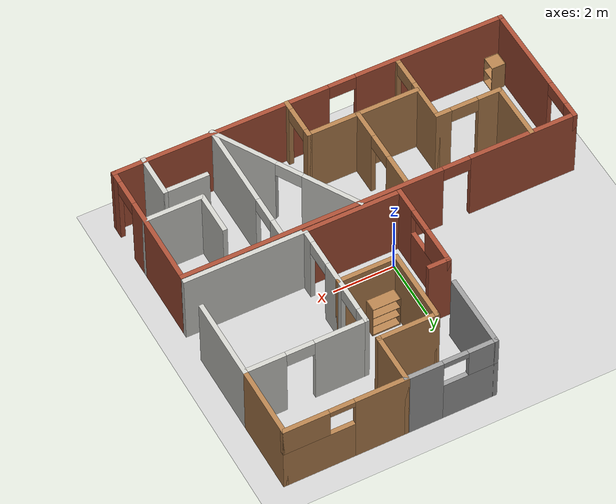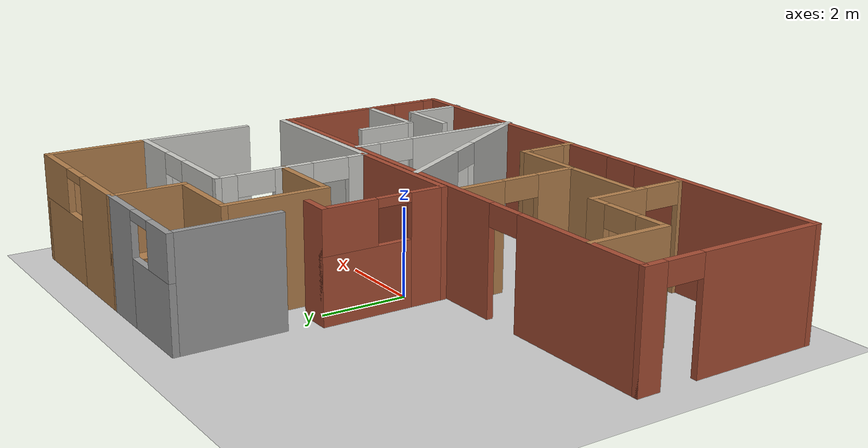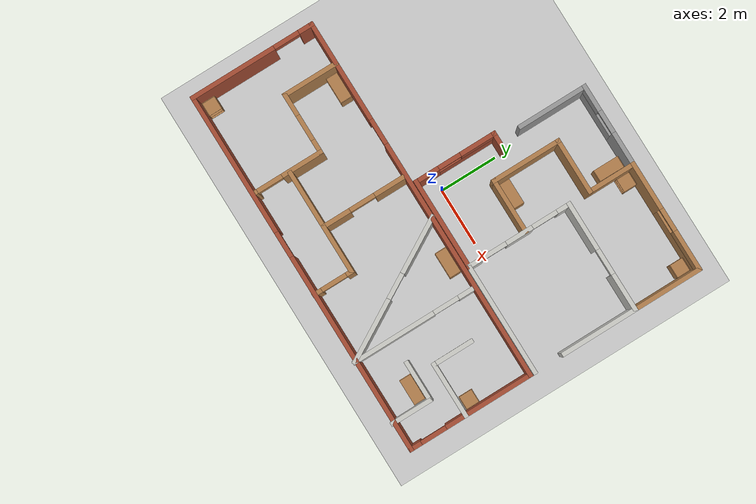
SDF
<sdf version="1.7">
 <world name="default">
  <light name="sun" type="directional">
   <pose>0 0 10 0 -0 0</pose>
   <diffuse>0.8 0.8 0.8 1</diffuse>
   <specular>0.2 0.2 0.2 1</specular>
   <attenuation>
    <range>1000</range>
    <constant>0.9</constant>
    <linear>0.01</linear>
    <quadratic>0.001</quadratic>
   </attenuation>
   <direction>-0.5 0.1 -0.9</direction>
   <spot><inner_angle>0</inner_angle><outer_angle>0</outer_angle><falloff>0</falloff></spot>
  </light>
  <model name="ground_plane">
   <static>1</static>
   <link name="link">
    <collision name="collision">
     <geometry><plane><normal>0 0 1</normal><size>100 100</size></plane></geometry>
     <surface><friction><ode><mu>100</mu><mu2>50</mu2></ode></friction></surface>
    </collision>
    <visual name="visual">
     <cast_shadows>0</cast_shadows>
     <geometry><plane><normal>0 0 1</normal><size>100 100</size></plane></geometry>
     <material>
      <script><uri>file://media/materials/scripts/gazebo.material</uri><name>Gazebo/Grey</name></script>
     </material>
    </visual>
   </link>
  </model>
  <gravity>0 0 -9.8</gravity>
  <magnetic_field>6e-06 2.3e-05 -4.2e-05</magnetic_field>
  <atmosphere type="adiabatic"/>
  <physics type="ode">
   <max_step_size>0.001</max_step_size>
   <real_time_factor>1</real_time_factor>
   <real_time_update_rate>1000</real_time_update_rate>
  </physics>
  <scene><ambient>0.4 0.4 0.4 1</ambient><background>0.7 0.7 0.7 1</background><shadows>1</shadows></scene>
  <audio><device>default</device></audio>
  <spherical_coordinates>
   <surface_model>EARTH_WGS84</surface_model>
   <latitude_deg>0</latitude_deg>
   <longitude_deg>0</longitude_deg>
   <elevation>0</elevation>
   <heading_deg>0</heading_deg>
  </spherical_coordinates>
  <model name="maze">
   <pose>0.010006 -2.63959 0 0 -0 0</pose>
   <link name="Wall_1">
    <pose>0 -2.49041 0 0 -0 0</pose>
    <visual name="Wall_1_Visual_0">
     <pose>-3.9975 0 1.25 0 -0 0</pose>
     <geometry><box><size>5.005 0.15 2.5</size></box></geometry>
     <material>
      <script><uri>file://media/materials/scripts/gazebo.material</uri><name>Gazebo/Bricks</name></script>
      <ambient>1 1 1 1</ambient>
     </material>
     <meta><layer>0</layer></meta>
    </visual>
    <collision name="Wall_1_Collision_0">
     <geometry><box><size>5.005 0.15 2.5</size></box></geometry>
     <pose>-3.9975 0 1.25 0 -0 0</pose>
    </collision>
    <visual name="Wall_1_Visual_1">
     <pose>2.9525 0 1.25 0 -0 0</pose>
     <geometry><box><size>7.095 0.15 2.5</size></box></geometry>
     <material>
      <script><uri>file://media/materials/scripts/gazebo.material</uri><name>Gazebo/Bricks</name></script>
      <ambient>1 1 1 1</ambient>
     </material>
     <meta><layer>0</layer></meta>
    </visual>
    <collision name="Wall_1_Collision_1">
     <geometry><box><size>7.095 0.15 2.5</size></box></geometry>
     <pose>2.9525 0 1.25 0 -0 0</pose>
    </collision>
    <visual name="Wall_1_Visual_2">
     <pose>-1.045 0 2.25 0 -0 0</pose>
     <geometry><box><size>0.9 0.15 0.5</size></box></geometry>
     <material>
      <script><uri>file://media/materials/scripts/gazebo.material</uri><name>Gazebo/Bricks</name></script>
      <ambient>1 1 1 1</ambient>
     </material>
     <meta><layer>0</layer></meta>
    </visual>
    <collision name="Wall_1_Collision_2">
     <geometry><box><size>0.9 0.15 0.5</size></box></geometry>
     <pose>-1.045 0 2.25 0 -0 0</pose>
    </collision>
   </link>
   <link name="Wall_10">
    <pose>-3.935 -0.010409 0 0 -0 0</pose>
    <visual name="Wall_10_Visual_0">
     <pose>-0.7125 0 1.25 0 -0 0</pose>
     <geometry><box><size>0.825 0.15 2.5</size></box></geometry>
     <material>
      <script><uri>file://media/materials/scripts/gazebo.material</uri><name>Gazebo/Wood</name></script>
      <ambient>1 1 1 1</ambient>
     </material>
     <meta><layer>0</layer></meta>
    </visual>
    <collision name="Wall_10_Collision_0">
     <geometry><box><size>0.825 0.15 2.5</size></box></geometry>
     <pose>-0.7125 0 1.25 0 -0 0</pose>
    </collision>
    <visual name="Wall_10_Visual_1">
     <pose>0.8625 0 1.25 0 -0 0</pose>
     <geometry><box><size>0.525 0.15 2.5</size></box></geometry>
     <material>
      <script><uri>file://media/materials/scripts/gazebo.material</uri><name>Gazebo/Wood</name></script>
      <ambient>1 1 1 1</ambient>
     </material>
     <meta><layer>0</layer></meta>
    </visual>
    <collision name="Wall_10_Collision_1">
     <geometry><box><size>0.525 0.15 2.5</size></box></geometry>
     <pose>0.8625 0 1.25 0 -0 0</pose>
    </collision>
    <visual name="Wall_10_Visual_2">
     <pose>0.15 0 2.25 0 -0 0</pose>
     <geometry><box><size>0.9 0.15 0.5</size></box></geometry>
     <material>
      <script><uri>file://media/materials/scripts/gazebo.material</uri><name>Gazebo/Wood</name></script>
      <ambient>1 1 1 1</ambient>
     </material>
     <meta><layer>0</layer></meta>
    </visual>
    <collision name="Wall_10_Collision_2">
     <geometry><box><size>0.9 0.15 0.5</size></box></geometry>
     <pose>0.15 0 2.25 0 -0 0</pose>
    </collision>
   </link>
   <link name="Wall_11">
    <pose>-2.885 -1.18541 0 0 -0 -1.5708</pose>
    <visual name="Wall_11_Visual_0">
     <pose>-0.5075 0 1.25 0 -0 0</pose>
     <geometry><box><size>1.485 0.15 2.5</size></box></geometry>
     <material>
      <script><uri>file://media/materials/scripts/gazebo.material</uri><name>Gazebo/Wood</name></script>
      <ambient>1 1 1 1</ambient>
     </material>
     <meta><layer>0</layer></meta>
    </visual>
    <collision name="Wall_11_Collision_0">
     <geometry><box><size>1.485 0.15 2.5</size></box></geometry>
     <pose>-0.5075 0 1.25 0 -0 0</pose>
    </collision>
    <visual name="Wall_11_Visual_1">
     <pose>1.1925 0 1.25 0 -0 0</pose>
     <geometry><box><size>0.115 0.15 2.5</size></box></geometry>
     <material>
      <script><uri>file://media/materials/scripts/gazebo.material</uri><name>Gazebo/Wood</name></script>
      <ambient>1 1 1 1</ambient>
     </material>
     <meta><layer>0</layer></meta>
    </visual>
    <collision name="Wall_11_Collision_1">
     <geometry><box><size>0.115 0.15 2.5</size></box></geometry>
     <pose>1.1925 0 1.25 0 -0 0</pose>
    </collision>
    <visual name="Wall_11_Visual_2">
     <pose>0.685 0 2.25 0 -0 0</pose>
     <geometry><box><size>0.9 0.15 0.5</size></box></geometry>
     <material>
      <script><uri>file://media/materials/scripts/gazebo.material</uri><name>Gazebo/Wood</name></script>
      <ambient>1 1 1 1</ambient>
     </material>
     <meta><layer>0</layer></meta>
    </visual>
    <collision name="Wall_11_Collision_2">
     <geometry><box><size>0.9 0.15 0.5</size></box></geometry>
     <pose>0.685 0 2.25 0 -0 0</pose>
    </collision>
   </link>
   <link name="Wall_16">
    <collision name="Wall_16_Collision">
     <geometry><box><size>3.75 0.15 2.5</size></box></geometry>
     <pose>0 0 1.25 0 -0 0</pose>
    </collision>
    <visual name="Wall_16_Visual">
     <pose>0 0 1.25 0 -0 0</pose>
     <geometry><box><size>3.75 0.15 2.5</size></box></geometry>
     <material>
      <script><uri>file://media/materials/scripts/gazebo.material</uri><name>Gazebo/Wood</name></script>
      <ambient>1 1 1 1</ambient>
     </material>
     <meta><layer>0</layer></meta>
    </visual>
    <pose>-1.025 -1.15041 0 0 -0 0</pose>
   </link>
   <link name="Wall_17">
    <pose>0.775 -1.82541 0 0 -0 -1.5708</pose>
    <visual name="Wall_17_Visual_0">
     <pose>-0.6175 0 1.25 0 -0 0</pose>
     <geometry><box><size>0.265 0.15 2.5</size></box></geometry>
     <material>
      <script><uri>file://media/materials/scripts/gazebo.material</uri><name>Gazebo/Wood</name></script>
      <ambient>1 1 1 1</ambient>
     </material>
     <meta><layer>0</layer></meta>
    </visual>
    <collision name="Wall_17_Collision_0">
     <geometry><box><size>0.265 0.15 2.5</size></box></geometry>
     <pose>-0.6175 0 1.25 0 -0 0</pose>
    </collision>
    <visual name="Wall_17_Visual_1">
     <pose>0.5825 0 1.25 0 -0 0</pose>
     <geometry><box><size>0.335 0.15 2.5</size></box></geometry>
     <material>
      <script><uri>file://media/materials/scripts/gazebo.material</uri><name>Gazebo/Wood</name></script>
      <ambient>1 1 1 1</ambient>
     </material>
     <meta><layer>0</layer></meta>
    </visual>
    <collision name="Wall_17_Collision_1">
     <geometry><box><size>0.335 0.15 2.5</size></box></geometry>
     <pose>0.5825 0 1.25 0 -0 0</pose>
    </collision>
    <visual name="Wall_17_Visual_2">
     <pose>-0.035 0 2.25 0 -0 0</pose>
     <geometry><box><size>0.9 0.15 0.5</size></box></geometry>
     <material>
      <script><uri>file://media/materials/scripts/gazebo.material</uri><name>Gazebo/Wood</name></script>
      <ambient>1 1 1 1</ambient>
     </material>
     <meta><layer>0</layer></meta>
    </visual>
    <collision name="Wall_17_Collision_2">
     <geometry><box><size>0.9 0.15 0.5</size></box></geometry>
     <pose>-0.035 0 2.25 0 -0 0</pose>
    </collision>
   </link>
   <link name="Wall_19">
    <pose>-0.865 0.304591 0 0 -0 1.5708</pose>
    <visual name="Wall_19_Visual_0">
     <pose>-0.9975 0 1.25 0 -0 0</pose>
     <geometry><box><size>1.005 0.15 2.5</size></box></geometry>
     <material>
      <script><uri>file://media/materials/scripts/gazebo.material</uri><name>Gazebo/Wood</name></script>
      <ambient>1 1 1 1</ambient>
     </material>
     <meta><layer>0</layer></meta>
    </visual>
    <collision name="Wall_19_Collision_0">
     <geometry><box><size>1.005 0.15 2.5</size></box></geometry>
     <pose>-0.9975 0 1.25 0 -0 0</pose>
    </collision>
    <visual name="Wall_19_Visual_1">
     <pose>0.9525 0 1.25 0 -0 0</pose>
     <geometry><box><size>1.095 0.15 2.5</size></box></geometry>
     <material>
      <script><uri>file://media/materials/scripts/gazebo.material</uri><name>Gazebo/Wood</name></script>
      <ambient>1 1 1 1</ambient>
     </material>
     <meta><layer>0</layer></meta>
    </visual>
    <collision name="Wall_19_Collision_1">
     <geometry><box><size>1.095 0.15 2.5</size></box></geometry>
     <pose>0.9525 0 1.25 0 -0 0</pose>
    </collision>
    <visual name="Wall_19_Visual_2">
     <pose>-0.045 0 2.25 0 -0 0</pose>
     <geometry><box><size>0.9 0.15 0.5</size></box></geometry>
     <material>
      <script><uri>file://media/materials/scripts/gazebo.material</uri><name>Gazebo/Wood</name></script>
      <ambient>1 1 1 1</ambient>
     </material>
     <meta><layer>0</layer></meta>
    </visual>
    <collision name="Wall_19_Collision_2">
     <geometry><box><size>0.9 0.15 0.5</size></box></geometry>
     <pose>-0.045 0 2.25 0 -0 0</pose>
    </collision>
   </link>
   <link name="Wall_21">
    <pose>1.94 -0.328774 0 0 -0 -1.0472</pose>
    <visual name="Wall_21_Visual_0">
     <pose>-1.595 0 1.25 0 -0 0</pose>
     <geometry><box><size>2.05999 0.15 2.5</size></box></geometry>
     <material>
      <script><uri>file://media/materials/scripts/gazebo.material</uri><name>Gazebo/CeilingTiled</name></script>
      <ambient>1 1 1 1</ambient>
     </material>
     <meta><layer>0</layer></meta>
    </visual>
    <collision name="Wall_21_Collision_0">
     <geometry><box><size>2.05999 0.15 2.5</size></box></geometry>
     <pose>-1.595 0 1.25 0 -0 0</pose>
    </collision>
    <visual name="Wall_21_Visual_1">
     <pose>1.48 0 1.25 0 -0 0</pose>
     <geometry><box><size>2.29001 0.15 2.5</size></box></geometry>
     <material>
      <script><uri>file://media/materials/scripts/gazebo.material</uri><name>Gazebo/CeilingTiled</name></script>
      <ambient>1 1 1 1</ambient>
     </material>
     <meta><layer>0</layer></meta>
    </visual>
    <collision name="Wall_21_Collision_1">
     <geometry><box><size>2.29001 0.15 2.5</size></box></geometry>
     <pose>1.48 0 1.25 0 -0 0</pose>
    </collision>
    <visual name="Wall_21_Visual_2">
     <pose>-0.115007 0 2.25 0 -0 0</pose>
     <geometry><box><size>0.9 0.15 0.5</size></box></geometry>
     <material>
      <script><uri>file://media/materials/scripts/gazebo.material</uri><name>Gazebo/CeilingTiled</name></script>
      <ambient>1 1 1 1</ambient>
     </material>
     <meta><layer>0</layer></meta>
    </visual>
    <collision name="Wall_21_Collision_2">
     <geometry><box><size>0.9 0.15 0.5</size></box></geometry>
     <pose>-0.115007 0 2.25 0 -0 0</pose>
    </collision>
   </link>
   <link name="Wall_22">
    <pose>3.215 -0.362139 0 0 -0 1.5708</pose>
    <visual name="Wall_22_Visual_0">
     <pose>-0.774135 0 1.25 0 -0 0</pose>
     <geometry><box><size>2.95173 0.15 2.5</size></box></geometry>
     <material>
      <script><uri>file://media/materials/scripts/gazebo.material</uri><name>Gazebo/CeilingTiled</name></script>
      <ambient>1 1 1 1</ambient>
     </material>
     <meta><layer>0</layer></meta>
    </visual>
    <collision name="Wall_22_Collision_0">
     <geometry><box><size>2.95173 0.15 2.5</size></box></geometry>
     <pose>-0.774135 0 1.25 0 -0 0</pose>
    </collision>
    <visual name="Wall_22_Visual_1">
     <pose>1.92586 0 1.25 0 -0 0</pose>
     <geometry><box><size>0.648271 0.15 2.5</size></box></geometry>
     <material>
      <script><uri>file://media/materials/scripts/gazebo.material</uri><name>Gazebo/CeilingTiled</name></script>
      <ambient>1 1 1 1</ambient>
     </material>
     <meta><layer>0</layer></meta>
    </visual>
    <collision name="Wall_22_Collision_1">
     <geometry><box><size>0.648271 0.15 2.5</size></box></geometry>
     <pose>1.92586 0 1.25 0 -0 0</pose>
    </collision>
    <visual name="Wall_22_Visual_2">
     <pose>1.15173 0 2.25 0 -0 0</pose>
     <geometry><box><size>0.9 0.15 0.5</size></box></geometry>
     <material>
      <script><uri>file://media/materials/scripts/gazebo.material</uri><name>Gazebo/CeilingTiled</name></script>
      <ambient>1 1 1 1</ambient>
     </material>
     <meta><layer>0</layer></meta>
    </visual>
    <collision name="Wall_22_Collision_2">
     <geometry><box><size>0.9 0.15 0.5</size></box></geometry>
     <pose>1.15173 0 2.25 0 -0 0</pose>
    </collision>
   </link>
   <link name="Wall_24">
    <collision name="Wall_24_Collision">
     <geometry><box><size>2 0.15 2.5</size></box></geometry>
     <pose>0 0 1.25 0 -0 0</pose>
    </collision>
    <visual name="Wall_24_Visual">
     <pose>0 0 1.25 0 -0 0</pose>
     <geometry><box><size>2 0.15 2.5</size></box></geometry>
     <material>
      <script><uri>file://media/materials/scripts/gazebo.material</uri><name>Gazebo/CeilingTiled</name></script>
      <ambient>1 1 1 1</ambient>
     </material>
     <meta><layer>0</layer></meta>
    </visual>
    <pose>5.5 -0.500409 0 0 -0 3.14159</pose>
   </link>
   <link name="Wall_25">
    <collision name="Wall_25_Collision">
     <geometry><box><size>1.5 0.15 2.5</size></box></geometry>
     <pose>0 0 1.25 0 -0 0</pose>
    </collision>
    <visual name="Wall_25_Visual">
     <pose>0 0 1.25 0 -0 0</pose>
     <geometry><box><size>1.5 0.15 2.5</size></box></geometry>
     <material>
      <script><uri>file://media/materials/scripts/gazebo.material</uri><name>Gazebo/CeilingTiled</name></script>
      <ambient>1 1 1 1</ambient>
     </material>
     <meta><layer>0</layer></meta>
    </visual>
    <pose>4.575 0.174591 0 0 -0 1.5708</pose>
   </link>
   <link name="Wall_27">
    <collision name="Wall_27_Collision">
     <geometry><box><size>1.5 0.15 2.5</size></box></geometry>
     <pose>0 0 1.25 0 -0 0</pose>
    </collision>
    <visual name="Wall_27_Visual">
     <pose>0 0 1.25 0 -0 0</pose>
     <geometry><box><size>1.5 0.15 2.5</size></box></geometry>
     <material>
      <script><uri>file://media/materials/scripts/gazebo.material</uri><name>Gazebo/CeilingTiled</name></script>
      <ambient>1 1 1 1</ambient>
     </material>
     <meta><layer>0</layer></meta>
    </visual>
    <pose>4.77 -1.19041 0 0 -0 0</pose>
   </link>
   <link name="Wall_28">
    <collision name="Wall_28_Collision">
     <geometry><box><size>1.5 0.15 2.5</size></box></geometry>
     <pose>0 0 1.25 0 -0 0</pose>
    </collision>
    <visual name="Wall_28_Visual">
     <pose>0 0 1.25 0 -0 0</pose>
     <geometry><box><size>1.5 0.15 2.5</size></box></geometry>
     <material>
      <script><uri>file://media/materials/scripts/gazebo.material</uri><name>Gazebo/CeilingTiled</name></script>
      <ambient>1 1 1 1</ambient>
     </material>
     <meta><layer>0</layer></meta>
    </visual>
    <pose>5.445 -1.86541 0 0 -0 -1.5708</pose>
   </link>
   <link name="Wall_5">
    <pose>-6.425 -0.315409 0 0 -0 1.5708</pose>
    <visual name="Wall_5_Visual_0">
     <pose>-0.7275 0 1.25 0 -0 0</pose>
     <geometry><box><size>3.045 0.15 2.5</size></box></geometry>
     <material>
      <script><uri>file://media/materials/scripts/gazebo.material</uri><name>Gazebo/Bricks</name></script>
      <ambient>1 1 1 1</ambient>
     </material>
     <meta><layer>0</layer></meta>
    </visual>
    <collision name="Wall_5_Collision_0">
     <geometry><box><size>3.045 0.15 2.5</size></box></geometry>
     <pose>-0.7275 0 1.25 0 -0 0</pose>
    </collision>
    <visual name="Wall_5_Visual_1">
     <pose>1.9725 0 1.25 0 -0 0</pose>
     <geometry><box><size>0.555 0.15 2.5</size></box></geometry>
     <material>
      <script><uri>file://media/materials/scripts/gazebo.material</uri><name>Gazebo/Bricks</name></script>
      <ambient>1 1 1 1</ambient>
     </material>
     <meta><layer>0</layer></meta>
    </visual>
    <collision name="Wall_5_Collision_1">
     <geometry><box><size>0.555 0.15 2.5</size></box></geometry>
     <pose>1.9725 0 1.25 0 -0 0</pose>
    </collision>
    <visual name="Wall_5_Visual_2">
     <pose>1.245 0 2.25 0 -0 0</pose>
     <geometry><box><size>0.9 0.15 0.5</size></box></geometry>
     <material>
      <script><uri>file://media/materials/scripts/gazebo.material</uri><name>Gazebo/Bricks</name></script>
      <ambient>1 1 1 1</ambient>
     </material>
     <meta><layer>0</layer></meta>
    </visual>
    <collision name="Wall_5_Collision_2">
     <geometry><box><size>0.9 0.15 0.5</size></box></geometry>
     <pose>1.245 0 2.25 0 -0 0</pose>
    </collision>
   </link>
   <link name="Wall_6">
    <pose>0 1.85959 0 0 -0 0</pose>
    <visual name="Wall_6_Visual_0">
     <pose>-4.7125 0 1.25 0 -0 0</pose>
     <geometry><box><size>3.575 0.15 2.5</size></box></geometry>
     <material>
      <script><uri>file://media/materials/scripts/gazebo.material</uri><name>Gazebo/Bricks</name></script>
      <ambient>1 1 1 1</ambient>
     </material>
     <meta><layer>0</layer></meta>
    </visual>
    <collision name="Wall_6_Collision_0">
     <geometry><box><size>3.575 0.15 2.5</size></box></geometry>
     <pose>-4.7125 0 1.25 0 -0 0</pose>
    </collision>
    <visual name="Wall_6_Visual_1">
     <pose>2.2375 0 1.25 0 -0 0</pose>
     <geometry><box><size>8.525 0.15 2.5</size></box></geometry>
     <material>
      <script><uri>file://media/materials/scripts/gazebo.material</uri><name>Gazebo/Bricks</name></script>
      <ambient>1 1 1 1</ambient>
     </material>
     <meta><layer>0</layer></meta>
    </visual>
    <collision name="Wall_6_Collision_1">
     <geometry><box><size>8.525 0.15 2.5</size></box></geometry>
     <pose>2.2375 0 1.25 0 -0 0</pose>
    </collision>
    <visual name="Wall_6_Visual_2">
     <pose>-2.475 0 2.25 0 -0 0</pose>
     <geometry><box><size>0.9 0.15 0.5</size></box></geometry>
     <material>
      <script><uri>file://media/materials/scripts/gazebo.material</uri><name>Gazebo/Bricks</name></script>
      <ambient>1 1 1 1</ambient>
     </material>
     <meta><layer>0</layer></meta>
    </visual>
    <collision name="Wall_6_Collision_2">
     <geometry><box><size>0.9 0.15 0.5</size></box></geometry>
     <pose>-2.475 0 2.25 0 -0 0</pose>
    </collision>
   </link>
   <link name="Wall_7">
    <pose>6.425 -0.315409 0 0 -0 -1.5708</pose>
    <visual name="Wall_7_Visual_0">
     <pose>-0.6775 0 1.25 0 -0 0</pose>
     <geometry><box><size>3.145 0.15 2.5</size></box></geometry>
     <material>
      <script><uri>file://media/materials/scripts/gazebo.material</uri><name>Gazebo/Bricks</name></script>
      <ambient>1 1 1 1</ambient>
     </material>
     <meta><layer>0</layer></meta>
    </visual>
    <collision name="Wall_7_Collision_0">
     <geometry><box><size>3.145 0.15 2.5</size></box></geometry>
     <pose>-0.6775 0 1.25 0 -0 0</pose>
    </collision>
    <visual name="Wall_7_Visual_1">
     <pose>2.0225 0 1.25 0 -0 0</pose>
     <geometry><box><size>0.455 0.15 2.5</size></box></geometry>
     <material>
      <script><uri>file://media/materials/scripts/gazebo.material</uri><name>Gazebo/Bricks</name></script>
      <ambient>1 1 1 1</ambient>
     </material>
     <meta><layer>0</layer></meta>
    </visual>
    <collision name="Wall_7_Collision_1">
     <geometry><box><size>0.455 0.15 2.5</size></box></geometry>
     <pose>2.0225 0 1.25 0 -0 0</pose>
    </collision>
    <visual name="Wall_7_Visual_2">
     <pose>1.345 0 2.25 0 -0 0</pose>
     <geometry><box><size>0.9 0.15 0.5</size></box></geometry>
     <material>
      <script><uri>file://media/materials/scripts/gazebo.material</uri><name>Gazebo/Bricks</name></script>
      <ambient>1 1 1 1</ambient>
     </material>
     <meta><layer>0</layer></meta>
    </visual>
    <collision name="Wall_7_Collision_2">
     <geometry><box><size>0.9 0.15 0.5</size></box></geometry>
     <pose>1.345 0 2.25 0 -0 0</pose>
    </collision>
   </link>
   <link name="Wall_9">
    <collision name="Wall_9_Collision">
     <geometry><box><size>2 0.15 2.5</size></box></geometry>
     <pose>0 0 1.25 0 -0 0</pose>
    </collision>
    <visual name="Wall_9_Visual">
     <pose>0 0 1.25 0 -0 0</pose>
     <geometry><box><size>2 0.15 2.5</size></box></geometry>
     <material>
      <script><uri>file://media/materials/scripts/gazebo.material</uri><name>Gazebo/Wood</name></script>
      <ambient>1 1 1 1</ambient>
     </material>
     <meta><layer>0</layer></meta>
    </visual>
    <pose>-4.985 0.914591 0 0 -0 -1.5708</pose>
   </link>
   <static>1</static>
  </model>
  <model name="closed_room">
   <pose>2.96001 2.39593 0 0 -0 0</pose>
   <link name="Wall_0">
    <pose>-0.375 -1.175 0 0 -0 -1.5708</pose>
    <visual name="Wall_0_Visual_0">
     <pose>-1.648 0 1.25 0 -0 0</pose>
     <geometry><box><size>0.524006 0.15 2.5</size></box></geometry>
     <material>
      <script><uri>file://media/materials/scripts/gazebo.material</uri><name>Gazebo/CeilingTiled</name></script>
      <ambient>1 1 1 1</ambient>
     </material>
     <meta><layer>0</layer></meta>
    </visual>
    <collision name="Wall_0_Collision_0">
     <geometry><box><size>0.524006 0.15 2.5</size></box></geometry>
     <pose>-1.648 0 1.25 0 -0 0</pose>
    </collision>
    <visual name="Wall_0_Visual_1">
     <pose>-0.006994 0 1.25 0 -0 0</pose>
     <geometry><box><size>0.958001 0.15 2.5</size></box></geometry>
     <material>
      <script><uri>file://media/materials/scripts/gazebo.material</uri><name>Gazebo/CeilingTiled</name></script>
      <ambient>1 1 1 1</ambient>
     </material>
     <meta><layer>0</layer></meta>
    </visual>
    <collision name="Wall_0_Collision_1">
     <geometry><box><size>0.958001 0.15 2.5</size></box></geometry>
     <pose>-0.006994 0 1.25 0 -0 0</pose>
    </collision>
    <visual name="Wall_0_Visual_2">
     <pose>1.641 0 1.25 0 -0 0</pose>
     <geometry><box><size>0.537993 0.15 2.5</size></box></geometry>
     <material>
      <script><uri>file://media/materials/scripts/gazebo.material</uri><name>Gazebo/CeilingTiled</name></script>
      <ambient>1 1 1 1</ambient>
     </material>
     <meta><layer>0</layer></meta>
    </visual>
    <collision name="Wall_0_Collision_2">
     <geometry><box><size>0.537993 0.15 2.5</size></box></geometry>
     <pose>1.641 0 1.25 0 -0 0</pose>
    </collision>
    <visual name="Wall_0_Visual_3">
     <pose>-0.935994 0 2.25 0 -0 0</pose>
     <geometry><box><size>0.9 0.15 0.5</size></box></geometry>
     <material>
      <script><uri>file://media/materials/scripts/gazebo.material</uri><name>Gazebo/CeilingTiled</name></script>
      <ambient>1 1 1 1</ambient>
     </material>
     <meta><layer>0</layer></meta>
    </visual>
    <collision name="Wall_0_Collision_3">
     <geometry><box><size>0.9 0.15 0.5</size></box></geometry>
     <pose>-0.935994 0 2.25 0 -0 0</pose>
    </collision>
    <visual name="Wall_0_Visual_4">
     <pose>0.922007 0 2.25 0 -0 0</pose>
     <geometry><box><size>0.9 0.15 0.5</size></box></geometry>
     <material>
      <script><uri>file://media/materials/scripts/gazebo.material</uri><name>Gazebo/CeilingTiled</name></script>
      <ambient>1 1 1 1</ambient>
     </material>
     <meta><layer>0</layer></meta>
    </visual>
    <collision name="Wall_0_Collision_4">
     <geometry><box><size>0.9 0.15 0.5</size></box></geometry>
     <pose>0.922007 0 2.25 0 -0 0</pose>
    </collision>
   </link>
   <link name="Wall_1">
    <collision name="Wall_1_Collision">
     <geometry><box><size>4 0.15 2.5</size></box></geometry>
     <pose>0 0 1.25 0 -0 0</pose>
    </collision>
    <visual name="Wall_1_Visual">
     <pose>0 0 1.25 0 -0 0</pose>
     <geometry><box><size>4 0.15 2.5</size></box></geometry>
     <material>
      <script><uri>file://media/materials/scripts/gazebo.material</uri><name>Gazebo/CeilingTiled</name></script>
      <ambient>1 1 1 1</ambient>
     </material>
     <meta><layer>0</layer></meta>
    </visual>
    <pose>1.55 -3.01 0 0 -0 0</pose>
   </link>
   <link name="Wall_10">
    <pose>1.55 3.01 0 0 -0 0</pose>
    <visual name="Wall_10_Visual_0">
     <pose>-1.14373 0 1.25 0 -0 0</pose>
     <geometry><box><size>1.71255 0.15 2.5</size></box></geometry>
     <material>
      <script><uri>file://media/materials/scripts/gazebo.material</uri><name>Gazebo/Wood</name></script>
      <ambient>1 1 1 1</ambient>
     </material>
     <meta><layer>0</layer></meta>
    </visual>
    <collision name="Wall_10_Collision_0">
     <geometry><box><size>1.71255 0.15 2.5</size></box></geometry>
     <pose>-1.14373 0 1.25 0 -0 0</pose>
    </collision>
    <visual name="Wall_10_Visual_1">
     <pose>0.856275 0 0.75 0 -0 0</pose>
     <geometry><box><size>2.28745 0.15 1.5</size></box></geometry>
     <material>
      <script><uri>file://media/materials/scripts/gazebo.material</uri><name>Gazebo/Wood</name></script>
      <ambient>1 1 1 1</ambient>
     </material>
     <meta><layer>0</layer></meta>
    </visual>
    <collision name="Wall_10_Collision_1">
     <geometry><box><size>2.28745 0.15 1.5</size></box></geometry>
     <pose>0.856275 0 0.75 0 -0 0</pose>
    </collision>
    <visual name="Wall_10_Visual_2">
     <pose>1.25628 0 2 0 -0 0</pose>
     <geometry><box><size>1.48745 0.15 1</size></box></geometry>
     <material>
      <script><uri>file://media/materials/scripts/gazebo.material</uri><name>Gazebo/Wood</name></script>
      <ambient>1 1 1 1</ambient>
     </material>
     <meta><layer>0</layer></meta>
    </visual>
    <collision name="Wall_10_Collision_2">
     <geometry><box><size>1.48745 0.15 1</size></box></geometry>
     <pose>1.25628 0 2 0 -0 0</pose>
    </collision>
    <visual name="Wall_10_Visual_3">
     <pose>0.112549 0 2.4 0 -0 0</pose>
     <geometry><box><size>0.8 0.15 0.2</size></box></geometry>
     <material>
      <script><uri>file://media/materials/scripts/gazebo.material</uri><name>Gazebo/Wood</name></script>
      <ambient>1 1 1 1</ambient>
     </material>
     <meta><layer>0</layer></meta>
    </visual>
    <collision name="Wall_10_Collision_3">
     <geometry><box><size>0.8 0.15 0.2</size></box></geometry>
     <pose>0.112549 0 2.4 0 -0 0</pose>
    </collision>
   </link>
   <link name="Wall_11">
    <collision name="Wall_11_Collision">
     <geometry><box><size>2.5 0.15 2.5</size></box></geometry>
     <pose>0 0 1.25 0 -0 0</pose>
    </collision>
    <visual name="Wall_11_Visual">
     <pose>0 0 1.25 0 -0 0</pose>
     <geometry><box><size>2.5 0.15 2.5</size></box></geometry>
     <material>
      <script><uri>file://media/materials/scripts/gazebo.material</uri><name>Gazebo/Wood</name></script>
      <ambient>1 1 1 1</ambient>
     </material>
     <meta><layer>0</layer></meta>
    </visual>
    <pose>3.475 1.835 0 0 -0 -1.5708</pose>
   </link>
   <link name="Wall_13">
    <collision name="Wall_13_Collision">
     <geometry><box><size>1.75 0.15 2.5</size></box></geometry>
     <pose>0 0 1.25 0 -0 0</pose>
    </collision>
    <visual name="Wall_13_Visual">
     <pose>0 0 1.25 0 -0 0</pose>
     <geometry><box><size>1.75 0.15 2.5</size></box></geometry>
     <material>
      <script><uri>file://media/materials/scripts/gazebo.material</uri><name>Gazebo/Wood</name></script>
      <ambient>1 1 1 1</ambient>
     </material>
     <meta><layer>0</layer></meta>
    </visual>
    <pose>-0.375 2.21 0 0 -0 -1.5708</pose>
   </link>
   <link name="Wall_14">
    <collision name="Wall_14_Collision">
     <geometry><box><size>2 0.15 2.5</size></box></geometry>
     <pose>0 0 1.25 0 -0 0</pose>
    </collision>
    <visual name="Wall_14_Visual">
     <pose>0 0 1.25 0 -0 0</pose>
     <geometry><box><size>2 0.15 2.5</size></box></geometry>
     <material>
      <script><uri>file://media/materials/scripts/gazebo.material</uri><name>Gazebo/Wood</name></script>
      <ambient>1 1 1 1</ambient>
     </material>
     <meta><layer>0</layer></meta>
    </visual>
    <pose>-1.3 1.41 0 0 -0 3.14159</pose>
   </link>
   <link name="Wall_15">
    <collision name="Wall_15_Collision">
     <geometry><box><size>2.5 0.15 2.5</size></box></geometry>
     <pose>0 0 1.25 0 -0 0</pose>
    </collision>
    <visual name="Wall_15_Visual">
     <pose>0 0 1.25 0 -0 0</pose>
     <geometry><box><size>2.5 0.15 2.5</size></box></geometry>
     <material>
      <script><uri>file://media/materials/scripts/gazebo.material</uri><name>Gazebo/Wood</name></script>
      <ambient>1 1 1 1</ambient>
     </material>
     <meta><layer>0</layer></meta>
    </visual>
    <pose>-2.225 0.235 0 0 -0 -1.5708</pose>
   </link>
   <link name="Wall_16">
    <collision name="Wall_16_Collision">
     <geometry><box><size>2 0.15 2.5</size></box></geometry>
     <pose>0 0 1.25 0 -0 0</pose>
    </collision>
    <visual name="Wall_16_Visual">
     <pose>0 0 1.25 0 -0 0</pose>
     <geometry><box><size>2 0.15 2.5</size></box></geometry>
     <material>
      <script><uri>file://media/materials/scripts/gazebo.material</uri><name>Gazebo/Wood</name></script>
      <ambient>1 1 1 1</ambient>
     </material>
     <meta><layer>0</layer></meta>
    </visual>
    <pose>-1.3 -0.94 0 0 -0 0</pose>
   </link>
   <link name="Wall_18">
    <collision name="Wall_18_Collision">
     <geometry><box><size>3.25 0.15 2.5</size></box></geometry>
     <pose>0 0 1.25 0 -0 0</pose>
    </collision>
    <visual name="Wall_18_Visual">
     <pose>0 0 1.25 0 -0 0</pose>
     <geometry><box><size>3.25 0.15 2.5</size></box></geometry>
     <material>
      <script><uri>file://media/materials/scripts/gazebo.material</uri><name>Gazebo/Bricks</name></script>
      <ambient>1 1 1 1</ambient>
     </material>
     <meta><layer>0</layer></meta>
    </visual>
    <pose>-1.925 -3.01 0 0 -0 3.14159</pose>
   </link>
   <link name="Wall_19">
    <pose>-3.475 -1.585 0 0 -0 1.5708</pose>
    <visual name="Wall_19_Visual_0">
     <pose>-1.05478 0 1.25 0 -0 0</pose>
     <geometry><box><size>0.89045 0.15 2.5</size></box></geometry>
     <material>
      <script><uri>file://media/materials/scripts/gazebo.material</uri><name>Gazebo/Bricks</name></script>
      <ambient>1 1 1 1</ambient>
     </material>
     <meta><layer>0</layer></meta>
    </visual>
    <collision name="Wall_19_Collision_0">
     <geometry><box><size>0.89045 0.15 2.5</size></box></geometry>
     <pose>-1.05478 0 1.25 0 -0 0</pose>
    </collision>
    <visual name="Wall_19_Visual_1">
     <pose>0.445225 0 0.75 0 -0 0</pose>
     <geometry><box><size>2.10955 0.15 1.5</size></box></geometry>
     <material>
      <script><uri>file://media/materials/scripts/gazebo.material</uri><name>Gazebo/Bricks</name></script>
      <ambient>1 1 1 1</ambient>
     </material>
     <meta><layer>0</layer></meta>
    </visual>
    <collision name="Wall_19_Collision_1">
     <geometry><box><size>2.10955 0.15 1.5</size></box></geometry>
     <pose>0.445225 0 0.75 0 -0 0</pose>
    </collision>
    <visual name="Wall_19_Visual_2">
     <pose>0.845225 0 2 0 -0 0</pose>
     <geometry><box><size>1.30955 0.15 1</size></box></geometry>
     <material>
      <script><uri>file://media/materials/scripts/gazebo.material</uri><name>Gazebo/Bricks</name></script>
      <ambient>1 1 1 1</ambient>
     </material>
     <meta><layer>0</layer></meta>
    </visual>
    <collision name="Wall_19_Collision_2">
     <geometry><box><size>1.30955 0.15 1</size></box></geometry>
     <pose>0.845225 0 2 0 -0 0</pose>
    </collision>
    <visual name="Wall_19_Visual_3">
     <pose>-0.20955 0 2.4 0 -0 0</pose>
     <geometry><box><size>0.8 0.15 0.2</size></box></geometry>
     <material>
      <script><uri>file://media/materials/scripts/gazebo.material</uri><name>Gazebo/Bricks</name></script>
      <ambient>1 1 1 1</ambient>
     </material>
     <meta><layer>0</layer></meta>
    </visual>
    <collision name="Wall_19_Collision_3">
     <geometry><box><size>0.8 0.15 0.2</size></box></geometry>
     <pose>-0.20955 0 2.4 0 -0 0</pose>
    </collision>
   </link>
   <link name="Wall_21">
    <collision name="Wall_21_Collision">
     <geometry><box><size>0.75 0.15 2.5</size></box></geometry>
     <pose>0 0 1.25 0 -0 0</pose>
    </collision>
    <visual name="Wall_21_Visual">
     <pose>0 0 1.25 0 -0 0</pose>
     <geometry><box><size>0.75 0.15 2.5</size></box></geometry>
     <material>
      <script><uri>file://media/materials/scripts/gazebo.material</uri><name>Gazebo/Bricks</name></script>
      <ambient>1 1 1 1</ambient>
     </material>
     <meta><layer>0</layer></meta>
    </visual>
    <pose>-3.175 -0.16 0 0 -0 0</pose>
   </link>
   <link name="Wall_29">
    <pose>-1.8 3.01 0 0 -0 3.14159</pose>
    <visual name="Wall_29_Visual_0">
     <pose>-0.881653 0 1.25 0 -0 0</pose>
     <geometry><box><size>1.23669 0.15 2.5</size></box></geometry>
     <material>
      <script><uri>file://media/materials/scripts/gazebo.material</uri><name>Gazebo/Grey</name></script>
      <ambient>1 1 1 1</ambient>
     </material>
     <meta><layer>0</layer></meta>
    </visual>
    <collision name="Wall_29_Collision_0">
     <geometry><box><size>1.23669 0.15 2.5</size></box></geometry>
     <pose>-0.881653 0 1.25 0 -0 0</pose>
    </collision>
    <visual name="Wall_29_Visual_1">
     <pose>0.618347 0 0.75 0 -0 0</pose>
     <geometry><box><size>1.76331 0.15 1.5</size></box></geometry>
     <material>
      <script><uri>file://media/materials/scripts/gazebo.material</uri><name>Gazebo/Grey</name></script>
      <ambient>1 1 1 1</ambient>
     </material>
     <meta><layer>0</layer></meta>
    </visual>
    <collision name="Wall_29_Collision_1">
     <geometry><box><size>1.76331 0.15 1.5</size></box></geometry>
     <pose>0.618347 0 0.75 0 -0 0</pose>
    </collision>
    <visual name="Wall_29_Visual_2">
     <pose>1.01835 0 2 0 -0 0</pose>
     <geometry><box><size>0.963306 0.15 1</size></box></geometry>
     <material>
      <script><uri>file://media/materials/scripts/gazebo.material</uri><name>Gazebo/Grey</name></script>
      <ambient>1 1 1 1</ambient>
     </material>
     <meta><layer>0</layer></meta>
    </visual>
    <collision name="Wall_29_Collision_2">
     <geometry><box><size>0.963306 0.15 1</size></box></geometry>
     <pose>1.01835 0 2 0 -0 0</pose>
    </collision>
    <visual name="Wall_29_Visual_3">
     <pose>0.136694 0 2.4 0 -0 0</pose>
     <geometry><box><size>0.8 0.15 0.2</size></box></geometry>
     <material>
      <script><uri>file://media/materials/scripts/gazebo.material</uri><name>Gazebo/Grey</name></script>
      <ambient>1 1 1 1</ambient>
     </material>
     <meta><layer>0</layer></meta>
    </visual>
    <collision name="Wall_29_Collision_3">
     <geometry><box><size>0.8 0.15 0.2</size></box></geometry>
     <pose>0.136694 0 2.4 0 -0 0</pose>
    </collision>
   </link>
   <link name="Wall_30">
    <collision name="Wall_30_Collision">
     <geometry><box><size>2.5 0.15 2.5</size></box></geometry>
     <pose>0 0 1.25 0 -0 0</pose>
    </collision>
    <visual name="Wall_30_Visual">
     <pose>0 0 1.25 0 -0 0</pose>
     <geometry><box><size>2.5 0.15 2.5</size></box></geometry>
     <material>
      <script><uri>file://media/materials/scripts/gazebo.material</uri><name>Gazebo/Grey</name></script>
      <ambient>1 1 1 1</ambient>
     </material>
     <meta><layer>0</layer></meta>
    </visual>
    <pose>-3.225 1.835 0 0 -0 -1.5708</pose>
   </link>
   <link name="Wall_6">
    <pose>1.55 0.66 0 0 -0 0</pose>
    <visual name="Wall_6_Visual_0">
     <pose>-1.1325 0 1.25 0 -0 0</pose>
     <geometry><box><size>1.735 0.15 2.5</size></box></geometry>
     <material>
      <script><uri>file://media/materials/scripts/gazebo.material</uri><name>Gazebo/CeilingTiled</name></script>
      <ambient>1 1 1 1</ambient>
     </material>
     <meta><layer>0</layer></meta>
    </visual>
    <collision name="Wall_6_Collision_0">
     <geometry><box><size>1.735 0.15 2.5</size></box></geometry>
     <pose>-1.1325 0 1.25 0 -0 0</pose>
    </collision>
    <visual name="Wall_6_Visual_1">
     <pose>1.3175 0 1.25 0 -0 0</pose>
     <geometry><box><size>1.365 0.15 2.5</size></box></geometry>
     <material>
      <script><uri>file://media/materials/scripts/gazebo.material</uri><name>Gazebo/CeilingTiled</name></script>
      <ambient>1 1 1 1</ambient>
     </material>
     <meta><layer>0</layer></meta>
    </visual>
    <collision name="Wall_6_Collision_1">
     <geometry><box><size>1.365 0.15 2.5</size></box></geometry>
     <pose>1.3175 0 1.25 0 -0 0</pose>
    </collision>
    <visual name="Wall_6_Visual_2">
     <pose>0.185 0 2.25 0 -0 0</pose>
     <geometry><box><size>0.9 0.15 0.5</size></box></geometry>
     <material>
      <script><uri>file://media/materials/scripts/gazebo.material</uri><name>Gazebo/CeilingTiled</name></script>
      <ambient>1 1 1 1</ambient>
     </material>
     <meta><layer>0</layer></meta>
    </visual>
    <collision name="Wall_6_Collision_2">
     <geometry><box><size>0.9 0.15 0.5</size></box></geometry>
     <pose>0.185 0 2.25 0 -0 0</pose>
    </collision>
   </link>
   <link name="Wall_7">
    <collision name="Wall_7_Collision">
     <geometry><box><size>2.75 0.15 2.5</size></box></geometry>
     <pose>0 0 1.25 0 -0 0</pose>
    </collision>
    <visual name="Wall_7_Visual">
     <pose>0 0 1.25 0 -0 0</pose>
     <geometry><box><size>2.75 0.15 2.5</size></box></geometry>
     <material>
      <script><uri>file://media/materials/scripts/gazebo.material</uri><name>Gazebo/CeilingTiled</name></script>
      <ambient>1 1 1 1</ambient>
     </material>
     <meta><layer>0</layer></meta>
    </visual>
    <pose>3.475 -0.64 0 0 -0 -1.5708</pose>
   </link>
   <static>1</static>
  </model>
  <model name="cabinet">
   <static>1</static>
   <link name="cabinet_bottom_plate">
    <inertial>
     <pose>0 0 -1 0 -0 0</pose>
     <inertia><ixx>2.05</ixx><ixy>0</ixy><ixz>0</ixz><iyy>2.05</iyy><iyz>0</iyz><izz>2.05</izz></inertia>
     <mass>25</mass>
    </inertial>
    <collision name="cabinet_bottom_plate_geom">
     <pose>0 0 0.01 0 -0 0</pose>
     <geometry><box><size>0.45 0.45 0.02</size></box></geometry>
    </collision>
    <visual name="cabinet_bottom_plate_geom_visual">
     <pose>0 0 0.01 0 -0 0</pose>
     <geometry><box><size>0.45 0.45 0.02</size></box></geometry>
     <material>
      <script><uri>file://media/materials/scripts/gazebo.material</uri><name>Gazebo/Wood</name></script>
     </material>
    </visual>
    <collision name="cabinet_bottom_plate_geom_cabinet_back_plate">
     <pose>0.235 0 0.51 0 -0 0</pose>
     <geometry><box><size>0.02 0.45 1.02</size></box></geometry>
    </collision>
    <visual name="cabinet_bottom_plate_geom_cabinet_back_plate_visual">
     <pose>0.235 0 0.51 0 -0 0</pose>
     <geometry><box><size>0.02 0.45 1.02</size></box></geometry>
     <material>
      <script><uri>file://media/materials/scripts/gazebo.material</uri><name>Gazebo/Wood</name></script>
     </material>
    </visual>
    <collision name="cabinet_bottom_plate_geom_cabinet_left_plate">
     <pose>0 0.235 0.51 0 -0 0</pose>
     <geometry><box><size>0.45 0.02 1.02</size></box></geometry>
    </collision>
    <visual name="cabinet_bottom_plate_geom_cabinet_left_plate_visual">
     <pose>0 0.235 0.51 0 -0 0</pose>
     <geometry><box><size>0.45 0.02 1.02</size></box></geometry>
     <material>
      <script><uri>file://media/materials/scripts/gazebo.material</uri><name>Gazebo/Wood</name></script>
     </material>
    </visual>
    <collision name="cabinet_bottom_plate_geom_cabinet_middle_plate">
     <pose>0 0 0.51 0 -0 0</pose>
     <geometry><box><size>0.45 0.45 0.02</size></box></geometry>
    </collision>
    <visual name="cabinet_bottom_plate_geom_cabinet_middle_plate_visual">
     <pose>0 0 0.51 0 -0 0</pose>
     <geometry><box><size>0.45 0.45 0.02</size></box></geometry>
     <material>
      <script><uri>file://media/materials/scripts/gazebo.material</uri><name>Gazebo/Wood</name></script>
     </material>
    </visual>
    <collision name="cabinet_bottom_plate_geom_cabinet_right_plate">
     <pose>0 -0.235 0.51 0 -0 0</pose>
     <geometry><box><size>0.45 0.02 1.02</size></box></geometry>
    </collision>
    <visual name="cabinet_bottom_plate_geom_cabinet_right_plate_visual">
     <pose>0 -0.235 0.51 0 -0 0</pose>
     <geometry><box><size>0.45 0.02 1.02</size></box></geometry>
     <material>
      <script><uri>file://media/materials/scripts/gazebo.material</uri><name>Gazebo/Wood</name></script>
     </material>
    </visual>
    <collision name="cabinet_bottom_plate_geom_cabinet_top_plate">
     <pose>0 0 1.01 0 -0 0</pose>
     <geometry><box><size>0.45 0.45 0.02</size></box></geometry>
    </collision>
    <visual name="cabinet_bottom_plate_geom_cabinet_top_plate_visual">
     <pose>0 0 1.01 0 -0 0</pose>
     <geometry><box><size>0.45 0.45 0.02</size></box></geometry>
     <material>
      <script><uri>file://media/materials/scripts/gazebo.material</uri><name>Gazebo/Wood</name></script>
     </material>
    </visual>
   </link>
   <pose>-6.07449 -4.8016 -0 0 -0 3.14159</pose>
  </model>
  <model name="bookshelf">
   <static>1</static>
   <link name="link">
    <inertial><mass>1</mass></inertial>
    <collision name="back">
     <pose>0 0.005 0.6 0 -0 0</pose>
     <geometry><box><size>0.9 0.01 1.2</size></box></geometry>
    </collision>
    <visual name="visual1">
     <pose>0 0.005 0.6 0 -0 0</pose>
     <geometry><box><size>0.9 0.01 1.2</size></box></geometry>
     <material>
      <script><uri>file://media/materials/scripts/gazebo.material</uri><name>Gazebo/Wood</name></script>
     </material>
    </visual>
    <collision name="left_side">
     <pose>0.45 -0.195 0.6 0 -0 0</pose>
     <geometry><box><size>0.02 0.4 1.2</size></box></geometry>
    </collision>
    <visual name="visual2">
     <pose>0.45 -0.195 0.6 0 -0 0</pose>
     <geometry><box><size>0.02 0.4 1.2</size></box></geometry>
     <material>
      <script><uri>file://media/materials/scripts/gazebo.material</uri><name>Gazebo/Wood</name></script>
     </material>
    </visual>
    <collision name="right_side">
     <pose>-0.45 -0.195 0.6 0 -0 0</pose>
     <geometry><box><size>0.02 0.4 1.2</size></box></geometry>
    </collision>
    <visual name="visual3">
     <pose>-0.45 -0.195 0.6 0 -0 0</pose>
     <geometry><box><size>0.02 0.4 1.2</size></box></geometry>
     <material>
      <script><uri>file://media/materials/scripts/gazebo.material</uri><name>Gazebo/Wood</name></script>
     </material>
    </visual>
    <collision name="bottom">
     <pose>0 -0.195 0.03 0 -0 0</pose>
     <geometry><box><size>0.88 0.4 0.06</size></box></geometry>
    </collision>
    <visual name="visual4">
     <pose>0 -0.195 0.03 0 -0 0</pose>
     <geometry><box><size>0.88 0.4 0.06</size></box></geometry>
     <material>
      <script><uri>file://media/materials/scripts/gazebo.material</uri><name>Gazebo/Wood</name></script>
     </material>
    </visual>
    <collision name="top">
     <pose>0 -0.195 1.19 0 -0 0</pose>
     <geometry><box><size>0.88 0.4 0.02</size></box></geometry>
    </collision>
    <visual name="visual5">
     <pose>0 -0.195 1.19 0 -0 0</pose>
     <geometry><box><size>0.88 0.4 0.02</size></box></geometry>
     <material>
      <script><uri>file://media/materials/scripts/gazebo.material</uri><name>Gazebo/Wood</name></script>
     </material>
    </visual>
    <collision name="low_shelf">
     <pose>0 -0.195 0.43 0 -0 0</pose>
     <geometry><box><size>0.88 0.4 0.02</size></box></geometry>
    </collision>
    <visual name="visual6">
     <pose>0 -0.195 0.43 0 -0 0</pose>
     <geometry><box><size>0.88 0.4 0.02</size></box></geometry>
     <material>
      <script><uri>file://media/materials/scripts/gazebo.material</uri><name>Gazebo/Wood</name></script>
     </material>
    </visual>
    <collision name="high_shelf">
     <pose>0 -0.195 0.8 0 -0 0</pose>
     <geometry><box><size>0.88 0.4 0.02</size></box></geometry>
    </collision>
    <visual name="visual7">
     <pose>0 -0.195 0.8 0 -0 0</pose>
     <geometry><box><size>0.88 0.4 0.02</size></box></geometry>
     <material>
      <script><uri>file://media/materials/scripts/gazebo.material</uri><name>Gazebo/Wood</name></script>
     </material>
    </visual>
   </link>
   <pose>-4.42673 -0.884151 0 0 -0 0</pose>
  </model>
  <model name="bookshelf_0">
   <static>1</static>
   <link name="link">
    <inertial><mass>1</mass></inertial>
    <collision name="back">
     <pose>0 0.005 0.6 0 -0 0</pose>
     <geometry><box><size>0.9 0.01 1.2</size></box></geometry>
    </collision>
    <visual name="visual1">
     <pose>0 0.005 0.6 0 -0 0</pose>
     <geometry><box><size>0.9 0.01 1.2</size></box></geometry>
     <material>
      <script><uri>file://media/materials/scripts/gazebo.material</uri><name>Gazebo/Wood</name></script>
     </material>
    </visual>
    <collision name="left_side">
     <pose>0.45 -0.195 0.6 0 -0 0</pose>
     <geometry><box><size>0.02 0.4 1.2</size></box></geometry>
    </collision>
    <visual name="visual2">
     <pose>0.45 -0.195 0.6 0 -0 0</pose>
     <geometry><box><size>0.02 0.4 1.2</size></box></geometry>
     <material>
      <script><uri>file://media/materials/scripts/gazebo.material</uri><name>Gazebo/Wood</name></script>
     </material>
    </visual>
    <collision name="right_side">
     <pose>-0.45 -0.195 0.6 0 -0 0</pose>
     <geometry><box><size>0.02 0.4 1.2</size></box></geometry>
    </collision>
    <visual name="visual3">
     <pose>-0.45 -0.195 0.6 0 -0 0</pose>
     <geometry><box><size>0.02 0.4 1.2</size></box></geometry>
     <material>
      <script><uri>file://media/materials/scripts/gazebo.material</uri><name>Gazebo/Wood</name></script>
     </material>
    </visual>
    <collision name="bottom">
     <pose>0 -0.195 0.03 0 -0 0</pose>
     <geometry><box><size>0.88 0.4 0.06</size></box></geometry>
    </collision>
    <visual name="visual4">
     <pose>0 -0.195 0.03 0 -0 0</pose>
     <geometry><box><size>0.88 0.4 0.06</size></box></geometry>
     <material>
      <script><uri>file://media/materials/scripts/gazebo.material</uri><name>Gazebo/Wood</name></script>
     </material>
    </visual>
    <collision name="top">
     <pose>0 -0.195 1.19 0 -0 0</pose>
     <geometry><box><size>0.88 0.4 0.02</size></box></geometry>
    </collision>
    <visual name="visual5">
     <pose>0 -0.195 1.19 0 -0 0</pose>
     <geometry><box><size>0.88 0.4 0.02</size></box></geometry>
     <material>
      <script><uri>file://media/materials/scripts/gazebo.material</uri><name>Gazebo/Wood</name></script>
     </material>
    </visual>
    <collision name="low_shelf">
     <pose>0 -0.195 0.43 0 -0 0</pose>
     <geometry><box><size>0.88 0.4 0.02</size></box></geometry>
    </collision>
    <visual name="visual6">
     <pose>0 -0.195 0.43 0 -0 0</pose>
     <geometry><box><size>0.88 0.4 0.02</size></box></geometry>
     <material>
      <script><uri>file://media/materials/scripts/gazebo.material</uri><name>Gazebo/Wood</name></script>
     </material>
    </visual>
    <collision name="high_shelf">
     <pose>0 -0.195 0.8 0 -0 0</pose>
     <geometry><box><size>0.88 0.4 0.02</size></box></geometry>
    </collision>
    <visual name="visual7">
     <pose>0 -0.195 0.8 0 -0 0</pose>
     <geometry><box><size>0.88 0.4 0.02</size></box></geometry>
     <material>
      <script><uri>file://media/materials/scripts/gazebo.material</uri><name>Gazebo/Wood</name></script>
     </material>
    </visual>
   </link>
   <pose>2.09368 -0.881671 0 0 -0 0</pose>
  </model>
  <model name="bookshelf_1">
   <static>1</static>
   <link name="link">
    <inertial><mass>1</mass></inertial>
    <collision name="back">
     <pose>0 0.005 0.6 0 -0 0</pose>
     <geometry><box><size>0.9 0.01 1.2</size></box></geometry>
    </collision>
    <visual name="visual1">
     <pose>0 0.005 0.6 0 -0 0</pose>
     <geometry><box><size>0.9 0.01 1.2</size></box></geometry>
     <material>
      <script><uri>file://media/materials/scripts/gazebo.material</uri><name>Gazebo/Wood</name></script>
     </material>
    </visual>
    <collision name="left_side">
     <pose>0.45 -0.195 0.6 0 -0 0</pose>
     <geometry><box><size>0.02 0.4 1.2</size></box></geometry>
    </collision>
    <visual name="visual2">
     <pose>0.45 -0.195 0.6 0 -0 0</pose>
     <geometry><box><size>0.02 0.4 1.2</size></box></geometry>
     <material>
      <script><uri>file://media/materials/scripts/gazebo.material</uri><name>Gazebo/Wood</name></script>
     </material>
    </visual>
    <collision name="right_side">
     <pose>-0.45 -0.195 0.6 0 -0 0</pose>
     <geometry><box><size>0.02 0.4 1.2</size></box></geometry>
    </collision>
    <visual name="visual3">
     <pose>-0.45 -0.195 0.6 0 -0 0</pose>
     <geometry><box><size>0.02 0.4 1.2</size></box></geometry>
     <material>
      <script><uri>file://media/materials/scripts/gazebo.material</uri><name>Gazebo/Wood</name></script>
     </material>
    </visual>
    <collision name="bottom">
     <pose>0 -0.195 0.03 0 -0 0</pose>
     <geometry><box><size>0.88 0.4 0.06</size></box></geometry>
    </collision>
    <visual name="visual4">
     <pose>0 -0.195 0.03 0 -0 0</pose>
     <geometry><box><size>0.88 0.4 0.06</size></box></geometry>
     <material>
      <script><uri>file://media/materials/scripts/gazebo.material</uri><name>Gazebo/Wood</name></script>
     </material>
    </visual>
    <collision name="top">
     <pose>0 -0.195 1.19 0 -0 0</pose>
     <geometry><box><size>0.88 0.4 0.02</size></box></geometry>
    </collision>
    <visual name="visual5">
     <pose>0 -0.195 1.19 0 -0 0</pose>
     <geometry><box><size>0.88 0.4 0.02</size></box></geometry>
     <material>
      <script><uri>file://media/materials/scripts/gazebo.material</uri><name>Gazebo/Wood</name></script>
     </material>
    </visual>
    <collision name="low_shelf">
     <pose>0 -0.195 0.43 0 -0 0</pose>
     <geometry><box><size>0.88 0.4 0.02</size></box></geometry>
    </collision>
    <visual name="visual6">
     <pose>0 -0.195 0.43 0 -0 0</pose>
     <geometry><box><size>0.88 0.4 0.02</size></box></geometry>
     <material>
      <script><uri>file://media/materials/scripts/gazebo.material</uri><name>Gazebo/Wood</name></script>
     </material>
    </visual>
    <collision name="high_shelf">
     <pose>0 -0.195 0.8 0 -0 0</pose>
     <geometry><box><size>0.88 0.4 0.02</size></box></geometry>
    </collision>
    <visual name="visual7">
     <pose>0 -0.195 0.8 0 -0 0</pose>
     <geometry><box><size>0.88 0.4 0.02</size></box></geometry>
     <material>
      <script><uri>file://media/materials/scripts/gazebo.material</uri><name>Gazebo/Wood</name></script>
     </material>
    </visual>
   </link>
   <pose>4.89263 -3.94786 0 0 -0 0</pose>
  </model>
  <model name="cabinet_0">
   <static>1</static>
   <link name="cabinet_bottom_plate">
    <inertial>
     <pose>0 0 -1 0 -0 0</pose>
     <inertia><ixx>2.05</ixx><ixy>0</ixy><ixz>0</ixz><iyy>2.05</iyy><iyz>0</iyz><izz>2.05</izz></inertia>
     <mass>25</mass>
    </inertial>
    <collision name="cabinet_bottom_plate_geom">
     <pose>0 0 0.01 0 -0 0</pose>
     <geometry><box><size>0.45 0.45 0.02</size></box></geometry>
    </collision>
    <visual name="cabinet_bottom_plate_geom_visual">
     <pose>0 0 0.01 0 -0 0</pose>
     <geometry><box><size>0.45 0.45 0.02</size></box></geometry>
     <material>
      <script><uri>file://media/materials/scripts/gazebo.material</uri><name>Gazebo/Wood</name></script>
     </material>
    </visual>
    <collision name="cabinet_bottom_plate_geom_cabinet_back_plate">
     <pose>0.235 0 0.51 0 -0 0</pose>
     <geometry><box><size>0.02 0.45 1.02</size></box></geometry>
    </collision>
    <visual name="cabinet_bottom_plate_geom_cabinet_back_plate_visual">
     <pose>0.235 0 0.51 0 -0 0</pose>
     <geometry><box><size>0.02 0.45 1.02</size></box></geometry>
     <material>
      <script><uri>file://media/materials/scripts/gazebo.material</uri><name>Gazebo/Wood</name></script>
     </material>
    </visual>
    <collision name="cabinet_bottom_plate_geom_cabinet_left_plate">
     <pose>0 0.235 0.51 0 -0 0</pose>
     <geometry><box><size>0.45 0.02 1.02</size></box></geometry>
    </collision>
    <visual name="cabinet_bottom_plate_geom_cabinet_left_plate_visual">
     <pose>0 0.235 0.51 0 -0 0</pose>
     <geometry><box><size>0.45 0.02 1.02</size></box></geometry>
     <material>
      <script><uri>file://media/materials/scripts/gazebo.material</uri><name>Gazebo/Wood</name></script>
     </material>
    </visual>
    <collision name="cabinet_bottom_plate_geom_cabinet_middle_plate">
     <pose>0 0 0.51 0 -0 0</pose>
     <geometry><box><size>0.45 0.45 0.02</size></box></geometry>
    </collision>
    <visual name="cabinet_bottom_plate_geom_cabinet_middle_plate_visual">
     <pose>0 0 0.51 0 -0 0</pose>
     <geometry><box><size>0.45 0.45 0.02</size></box></geometry>
     <material>
      <script><uri>file://media/materials/scripts/gazebo.material</uri><name>Gazebo/Wood</name></script>
     </material>
    </visual>
    <collision name="cabinet_bottom_plate_geom_cabinet_right_plate">
     <pose>0 -0.235 0.51 0 -0 0</pose>
     <geometry><box><size>0.45 0.02 1.02</size></box></geometry>
    </collision>
    <visual name="cabinet_bottom_plate_geom_cabinet_right_plate_visual">
     <pose>0 -0.235 0.51 0 -0 0</pose>
     <geometry><box><size>0.45 0.02 1.02</size></box></geometry>
     <material>
      <script><uri>file://media/materials/scripts/gazebo.material</uri><name>Gazebo/Wood</name></script>
     </material>
    </visual>
    <collision name="cabinet_bottom_plate_geom_cabinet_top_plate">
     <pose>0 0 1.01 0 -0 0</pose>
     <geometry><box><size>0.45 0.45 0.02</size></box></geometry>
    </collision>
    <visual name="cabinet_bottom_plate_geom_cabinet_top_plate_visual">
     <pose>0 0 1.01 0 -0 0</pose>
     <geometry><box><size>0.45 0.45 0.02</size></box></geometry>
     <material>
      <script><uri>file://media/materials/scripts/gazebo.material</uri><name>Gazebo/Wood</name></script>
     </material>
    </visual>
   </link>
   <pose>6.10288 5.05822 0 0 -0 0</pose>
  </model>
  <model name="cabinet_1">
   <static>1</static>
   <link name="cabinet_bottom_plate">
    <inertial>
     <pose>0 0 -1 0 -0 0</pose>
     <inertia><ixx>2.05</ixx><ixy>0</ixy><ixz>0</ixz><iyy>2.05</iyy><iyz>0</iyz><izz>2.05</izz></inertia>
     <mass>25</mass>
    </inertial>
    <collision name="cabinet_bottom_plate_geom">
     <pose>0 0 0.01 0 -0 0</pose>
     <geometry><box><size>0.45 0.45 0.02</size></box></geometry>
    </collision>
    <visual name="cabinet_bottom_plate_geom_visual">
     <pose>0 0 0.01 0 -0 0</pose>
     <geometry><box><size>0.45 0.45 0.02</size></box></geometry>
     <material>
      <script><uri>file://media/materials/scripts/gazebo.material</uri><name>Gazebo/Wood</name></script>
     </material>
    </visual>
    <collision name="cabinet_bottom_plate_geom_cabinet_back_plate">
     <pose>0.235 0 0.51 0 -0 0</pose>
     <geometry><box><size>0.02 0.45 1.02</size></box></geometry>
    </collision>
    <visual name="cabinet_bottom_plate_geom_cabinet_back_plate_visual">
     <pose>0.235 0 0.51 0 -0 0</pose>
     <geometry><box><size>0.02 0.45 1.02</size></box></geometry>
     <material>
      <script><uri>file://media/materials/scripts/gazebo.material</uri><name>Gazebo/Wood</name></script>
     </material>
    </visual>
    <collision name="cabinet_bottom_plate_geom_cabinet_left_plate">
     <pose>0 0.235 0.51 0 -0 0</pose>
     <geometry><box><size>0.45 0.02 1.02</size></box></geometry>
    </collision>
    <visual name="cabinet_bottom_plate_geom_cabinet_left_plate_visual">
     <pose>0 0.235 0.51 0 -0 0</pose>
     <geometry><box><size>0.45 0.02 1.02</size></box></geometry>
     <material>
      <script><uri>file://media/materials/scripts/gazebo.material</uri><name>Gazebo/Wood</name></script>
     </material>
    </visual>
    <collision name="cabinet_bottom_plate_geom_cabinet_middle_plate">
     <pose>0 0 0.51 0 -0 0</pose>
     <geometry><box><size>0.45 0.45 0.02</size></box></geometry>
    </collision>
    <visual name="cabinet_bottom_plate_geom_cabinet_middle_plate_visual">
     <pose>0 0 0.51 0 -0 0</pose>
     <geometry><box><size>0.45 0.45 0.02</size></box></geometry>
     <material>
      <script><uri>file://media/materials/scripts/gazebo.material</uri><name>Gazebo/Wood</name></script>
     </material>
    </visual>
    <collision name="cabinet_bottom_plate_geom_cabinet_right_plate">
     <pose>0 -0.235 0.51 0 -0 0</pose>
     <geometry><box><size>0.45 0.02 1.02</size></box></geometry>
    </collision>
    <visual name="cabinet_bottom_plate_geom_cabinet_right_plate_visual">
     <pose>0 -0.235 0.51 0 -0 0</pose>
     <geometry><box><size>0.45 0.02 1.02</size></box></geometry>
     <material>
      <script><uri>file://media/materials/scripts/gazebo.material</uri><name>Gazebo/Wood</name></script>
     </material>
    </visual>
    <collision name="cabinet_bottom_plate_geom_cabinet_top_plate">
     <pose>0 0 1.01 0 -0 0</pose>
     <geometry><box><size>0.45 0.45 0.02</size></box></geometry>
    </collision>
    <visual name="cabinet_bottom_plate_geom_cabinet_top_plate_visual">
     <pose>0 0 1.01 0 -0 0</pose>
     <geometry><box><size>0.45 0.45 0.02</size></box></geometry>
     <material>
      <script><uri>file://media/materials/scripts/gazebo.material</uri><name>Gazebo/Wood</name></script>
     </material>
    </visual>
   </link>
   <pose>2.91458 5.06902 0 0 -0 1.5708</pose>
  </model>
  <model name="bookshelf_2">
   <static>1</static>
   <link name="link">
    <inertial><mass>1</mass></inertial>
    <collision name="back">
     <pose>0 0.005 0.6 0 -0 0</pose>
     <geometry><box><size>0.9 0.01 1.2</size></box></geometry>
    </collision>
    <visual name="visual1">
     <pose>0 0.005 0.6 0 -0 0</pose>
     <geometry><box><size>0.9 0.01 1.2</size></box></geometry>
     <material>
      <script><uri>file://media/materials/scripts/gazebo.material</uri><name>Gazebo/Wood</name></script>
     </material>
    </visual>
    <collision name="left_side">
     <pose>0.45 -0.195 0.6 0 -0 0</pose>
     <geometry><box><size>0.02 0.4 1.2</size></box></geometry>
    </collision>
    <visual name="visual2">
     <pose>0.45 -0.195 0.6 0 -0 0</pose>
     <geometry><box><size>0.02 0.4 1.2</size></box></geometry>
     <material>
      <script><uri>file://media/materials/scripts/gazebo.material</uri><name>Gazebo/Wood</name></script>
     </material>
    </visual>
    <collision name="right_side">
     <pose>-0.45 -0.195 0.6 0 -0 0</pose>
     <geometry><box><size>0.02 0.4 1.2</size></box></geometry>
    </collision>
    <visual name="visual3">
     <pose>-0.45 -0.195 0.6 0 -0 0</pose>
     <geometry><box><size>0.02 0.4 1.2</size></box></geometry>
     <material>
      <script><uri>file://media/materials/scripts/gazebo.material</uri><name>Gazebo/Wood</name></script>
     </material>
    </visual>
    <collision name="bottom">
     <pose>0 -0.195 0.03 0 -0 0</pose>
     <geometry><box><size>0.88 0.4 0.06</size></box></geometry>
    </collision>
    <visual name="visual4">
     <pose>0 -0.195 0.03 0 -0 0</pose>
     <geometry><box><size>0.88 0.4 0.06</size></box></geometry>
     <material>
      <script><uri>file://media/materials/scripts/gazebo.material</uri><name>Gazebo/Wood</name></script>
     </material>
    </visual>
    <collision name="top">
     <pose>0 -0.195 1.19 0 -0 0</pose>
     <geometry><box><size>0.88 0.4 0.02</size></box></geometry>
    </collision>
    <visual name="visual5">
     <pose>0 -0.195 1.19 0 -0 0</pose>
     <geometry><box><size>0.88 0.4 0.02</size></box></geometry>
     <material>
      <script><uri>file://media/materials/scripts/gazebo.material</uri><name>Gazebo/Wood</name></script>
     </material>
    </visual>
    <collision name="low_shelf">
     <pose>0 -0.195 0.43 0 -0 0</pose>
     <geometry><box><size>0.88 0.4 0.02</size></box></geometry>
    </collision>
    <visual name="visual6">
     <pose>0 -0.195 0.43 0 -0 0</pose>
     <geometry><box><size>0.88 0.4 0.02</size></box></geometry>
     <material>
      <script><uri>file://media/materials/scripts/gazebo.material</uri><name>Gazebo/Wood</name></script>
     </material>
    </visual>
    <collision name="high_shelf">
     <pose>0 -0.195 0.8 0 -0 0</pose>
     <geometry><box><size>0.88 0.4 0.02</size></box></geometry>
    </collision>
    <visual name="visual7">
     <pose>0 -0.195 0.8 0 -0 0</pose>
     <geometry><box><size>0.88 0.4 0.02</size></box></geometry>
     <material>
      <script><uri>file://media/materials/scripts/gazebo.material</uri><name>Gazebo/Wood</name></script>
     </material>
    </visual>
   </link>
   <pose>1.3119 1.56872 0 0 -0 3.14159</pose>
  </model>
  <model name="bookshelf_3">
   <static>1</static>
   <link name="link">
    <inertial><mass>1</mass></inertial>
    <collision name="back">
     <pose>0 0.005 0.6 0 -0 0</pose>
     <geometry><box><size>0.9 0.01 1.2</size></box></geometry>
    </collision>
    <visual name="visual1">
     <pose>0 0.005 0.6 0 -0 0</pose>
     <geometry><box><size>0.9 0.01 1.2</size></box></geometry>
     <material>
      <script><uri>file://media/materials/scripts/gazebo.material</uri><name>Gazebo/Wood</name></script>
     </material>
    </visual>
    <collision name="left_side">
     <pose>0.45 -0.195 0.6 0 -0 0</pose>
     <geometry><box><size>0.02 0.4 1.2</size></box></geometry>
    </collision>
    <visual name="visual2">
     <pose>0.45 -0.195 0.6 0 -0 0</pose>
     <geometry><box><size>0.02 0.4 1.2</size></box></geometry>
     <material>
      <script><uri>file://media/materials/scripts/gazebo.material</uri><name>Gazebo/Wood</name></script>
     </material>
    </visual>
    <collision name="right_side">
     <pose>-0.45 -0.195 0.6 0 -0 0</pose>
     <geometry><box><size>0.02 0.4 1.2</size></box></geometry>
    </collision>
    <visual name="visual3">
     <pose>-0.45 -0.195 0.6 0 -0 0</pose>
     <geometry><box><size>0.02 0.4 1.2</size></box></geometry>
     <material>
      <script><uri>file://media/materials/scripts/gazebo.material</uri><name>Gazebo/Wood</name></script>
     </material>
    </visual>
    <collision name="bottom">
     <pose>0 -0.195 0.03 0 -0 0</pose>
     <geometry><box><size>0.88 0.4 0.06</size></box></geometry>
    </collision>
    <visual name="visual4">
     <pose>0 -0.195 0.03 0 -0 0</pose>
     <geometry><box><size>0.88 0.4 0.06</size></box></geometry>
     <material>
      <script><uri>file://media/materials/scripts/gazebo.material</uri><name>Gazebo/Wood</name></script>
     </material>
    </visual>
    <collision name="top">
     <pose>0 -0.195 1.19 0 -0 0</pose>
     <geometry><box><size>0.88 0.4 0.02</size></box></geometry>
    </collision>
    <visual name="visual5">
     <pose>0 -0.195 1.19 0 -0 0</pose>
     <geometry><box><size>0.88 0.4 0.02</size></box></geometry>
     <material>
      <script><uri>file://media/materials/scripts/gazebo.material</uri><name>Gazebo/Wood</name></script>
     </material>
    </visual>
    <collision name="low_shelf">
     <pose>0 -0.195 0.43 0 -0 0</pose>
     <geometry><box><size>0.88 0.4 0.02</size></box></geometry>
    </collision>
    <visual name="visual6">
     <pose>0 -0.195 0.43 0 -0 0</pose>
     <geometry><box><size>0.88 0.4 0.02</size></box></geometry>
     <material>
      <script><uri>file://media/materials/scripts/gazebo.material</uri><name>Gazebo/Wood</name></script>
     </material>
    </visual>
    <collision name="high_shelf">
     <pose>0 -0.195 0.8 0 -0 0</pose>
     <geometry><box><size>0.88 0.4 0.02</size></box></geometry>
    </collision>
    <visual name="visual7">
     <pose>0 -0.195 0.8 0 -0 0</pose>
     <geometry><box><size>0.88 0.4 0.02</size></box></geometry>
     <material>
      <script><uri>file://media/materials/scripts/gazebo.material</uri><name>Gazebo/Wood</name></script>
     </material>
    </visual>
   </link>
   <pose>2.46168 4.80122 0 0 0 -1.5708</pose>
  </model>
  <model name="cabinet_2">
   <static>1</static>
   <link name="cabinet_bottom_plate">
    <inertial>
     <pose>0 0 -1 0 -0 0</pose>
     <inertia><ixx>2.05</ixx><ixy>0</ixy><ixz>0</ixz><iyy>2.05</iyy><iyz>0</iyz><izz>2.05</izz></inertia>
     <mass>25</mass>
    </inertial>
    <collision name="cabinet_bottom_plate_geom">
     <pose>0 0 0.01 0 -0 0</pose>
     <geometry><box><size>0.45 0.45 0.02</size></box></geometry>
    </collision>
    <visual name="cabinet_bottom_plate_geom_visual">
     <pose>0 0 0.01 0 -0 0</pose>
     <geometry><box><size>0.45 0.45 0.02</size></box></geometry>
     <material>
      <script><uri>file://media/materials/scripts/gazebo.material</uri><name>Gazebo/Wood</name></script>
     </material>
    </visual>
    <collision name="cabinet_bottom_plate_geom_cabinet_back_plate">
     <pose>0.235 0 0.51 0 -0 0</pose>
     <geometry><box><size>0.02 0.45 1.02</size></box></geometry>
    </collision>
    <visual name="cabinet_bottom_plate_geom_cabinet_back_plate_visual">
     <pose>0.235 0 0.51 0 -0 0</pose>
     <geometry><box><size>0.02 0.45 1.02</size></box></geometry>
     <material>
      <script><uri>file://media/materials/scripts/gazebo.material</uri><name>Gazebo/Wood</name></script>
     </material>
    </visual>
    <collision name="cabinet_bottom_plate_geom_cabinet_left_plate">
     <pose>0 0.235 0.51 0 -0 0</pose>
     <geometry><box><size>0.45 0.02 1.02</size></box></geometry>
    </collision>
    <visual name="cabinet_bottom_plate_geom_cabinet_left_plate_visual">
     <pose>0 0.235 0.51 0 -0 0</pose>
     <geometry><box><size>0.45 0.02 1.02</size></box></geometry>
     <material>
      <script><uri>file://media/materials/scripts/gazebo.material</uri><name>Gazebo/Wood</name></script>
     </material>
    </visual>
    <collision name="cabinet_bottom_plate_geom_cabinet_middle_plate">
     <pose>0 0 0.51 0 -0 0</pose>
     <geometry><box><size>0.45 0.45 0.02</size></box></geometry>
    </collision>
    <visual name="cabinet_bottom_plate_geom_cabinet_middle_plate_visual">
     <pose>0 0 0.51 0 -0 0</pose>
     <geometry><box><size>0.45 0.45 0.02</size></box></geometry>
     <material>
      <script><uri>file://media/materials/scripts/gazebo.material</uri><name>Gazebo/Wood</name></script>
     </material>
    </visual>
    <collision name="cabinet_bottom_plate_geom_cabinet_right_plate">
     <pose>0 -0.235 0.51 0 -0 0</pose>
     <geometry><box><size>0.45 0.02 1.02</size></box></geometry>
    </collision>
    <visual name="cabinet_bottom_plate_geom_cabinet_right_plate_visual">
     <pose>0 -0.235 0.51 0 -0 0</pose>
     <geometry><box><size>0.45 0.02 1.02</size></box></geometry>
     <material>
      <script><uri>file://media/materials/scripts/gazebo.material</uri><name>Gazebo/Wood</name></script>
     </material>
    </visual>
    <collision name="cabinet_bottom_plate_geom_cabinet_top_plate">
     <pose>0 0 1.01 0 -0 0</pose>
     <geometry><box><size>0.45 0.45 0.02</size></box></geometry>
    </collision>
    <visual name="cabinet_bottom_plate_geom_cabinet_top_plate_visual">
     <pose>0 0 1.01 0 -0 0</pose>
     <geometry><box><size>0.45 0.45 0.02</size></box></geometry>
     <material>
      <script><uri>file://media/materials/scripts/gazebo.material</uri><name>Gazebo/Wood</name></script>
     </material>
    </visual>
   </link>
   <pose>6.09824 -2.79093 0 0 -0 0</pose>
  </model>
 </world>
</sdf>
